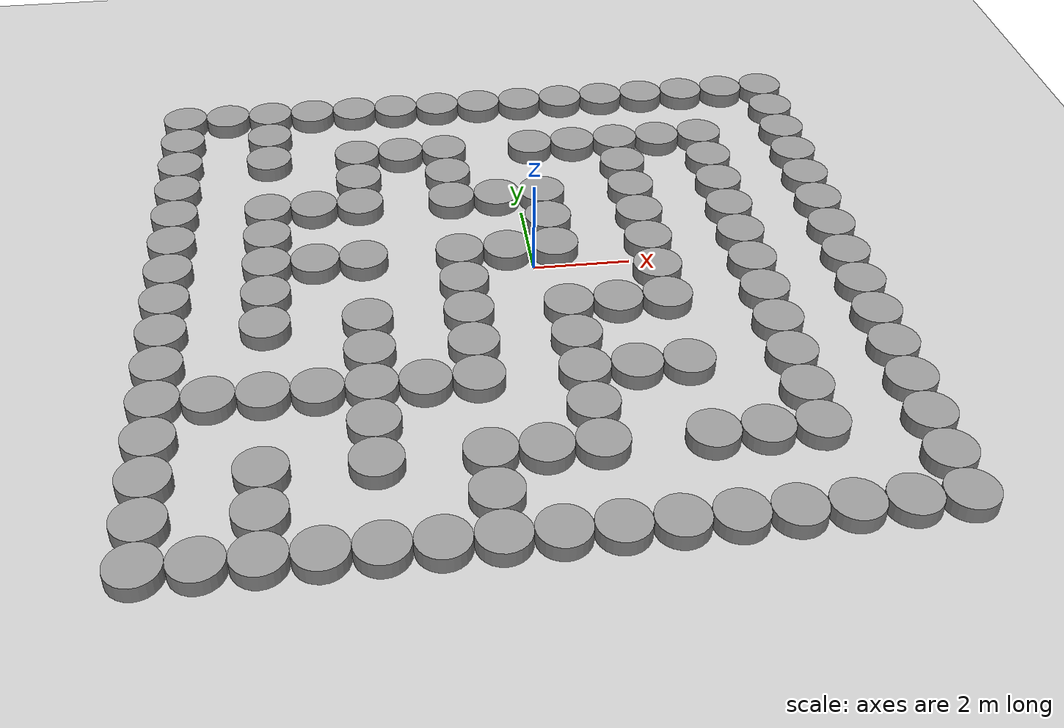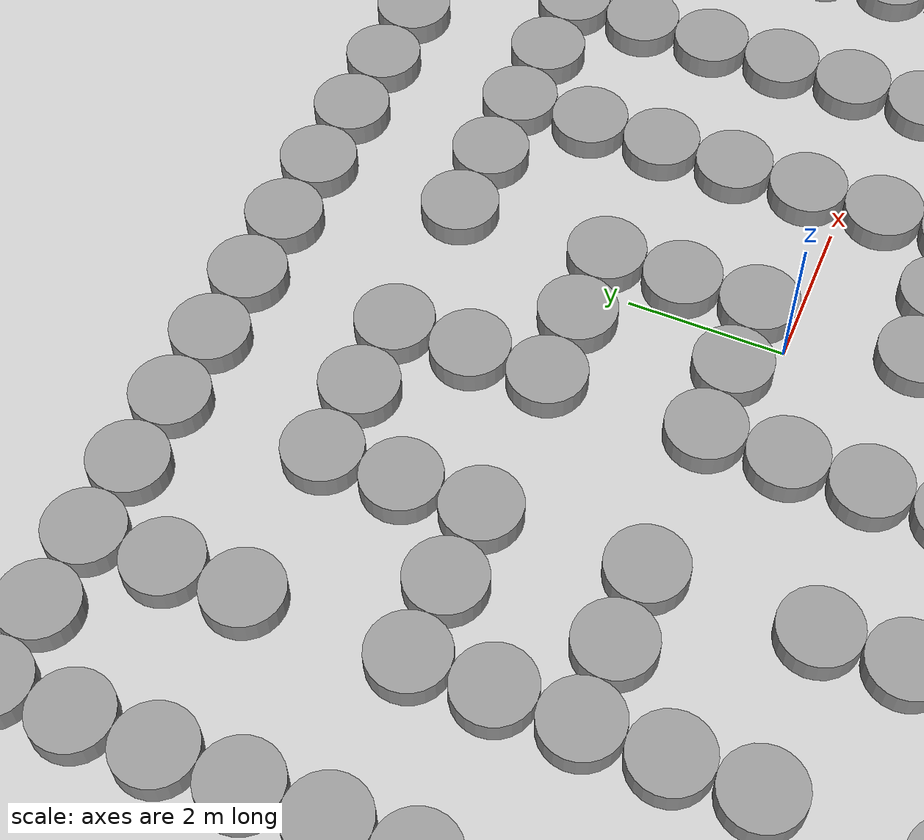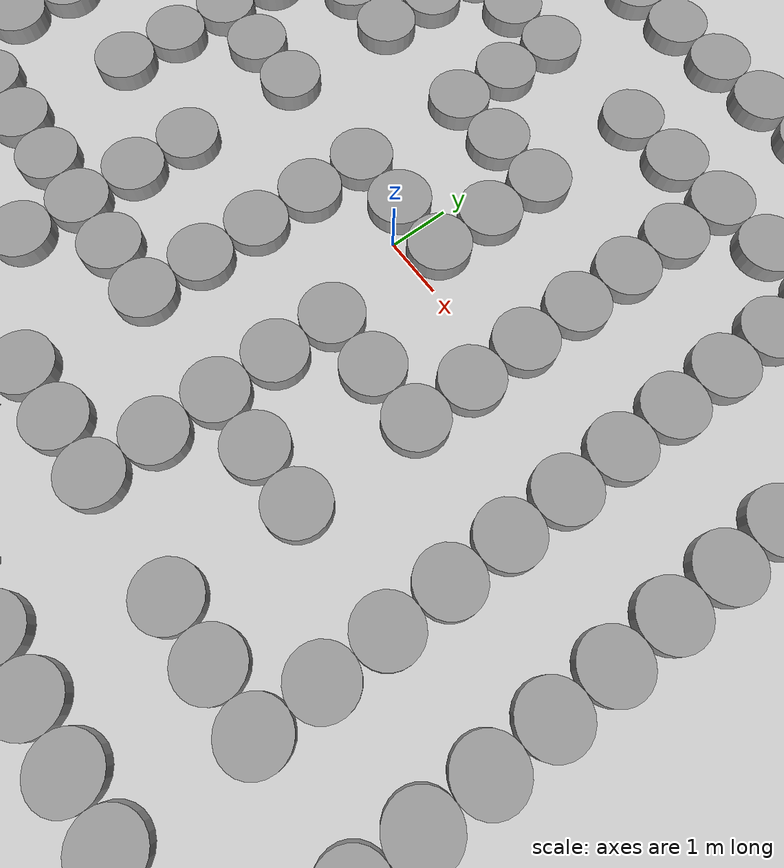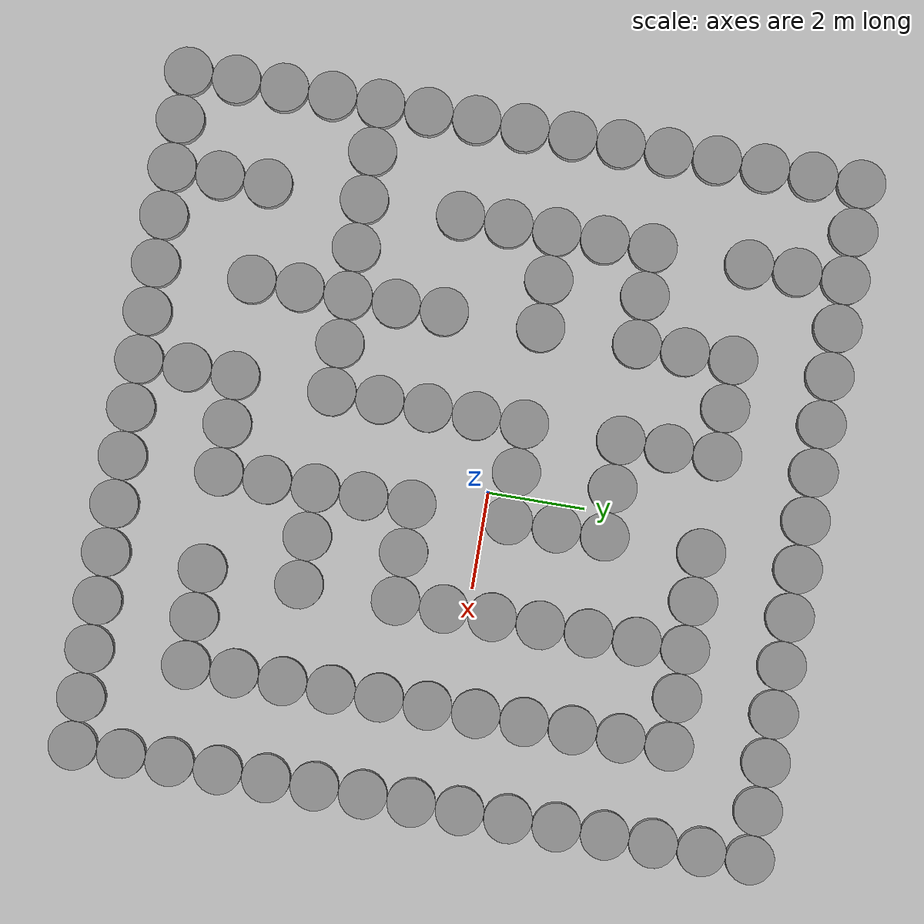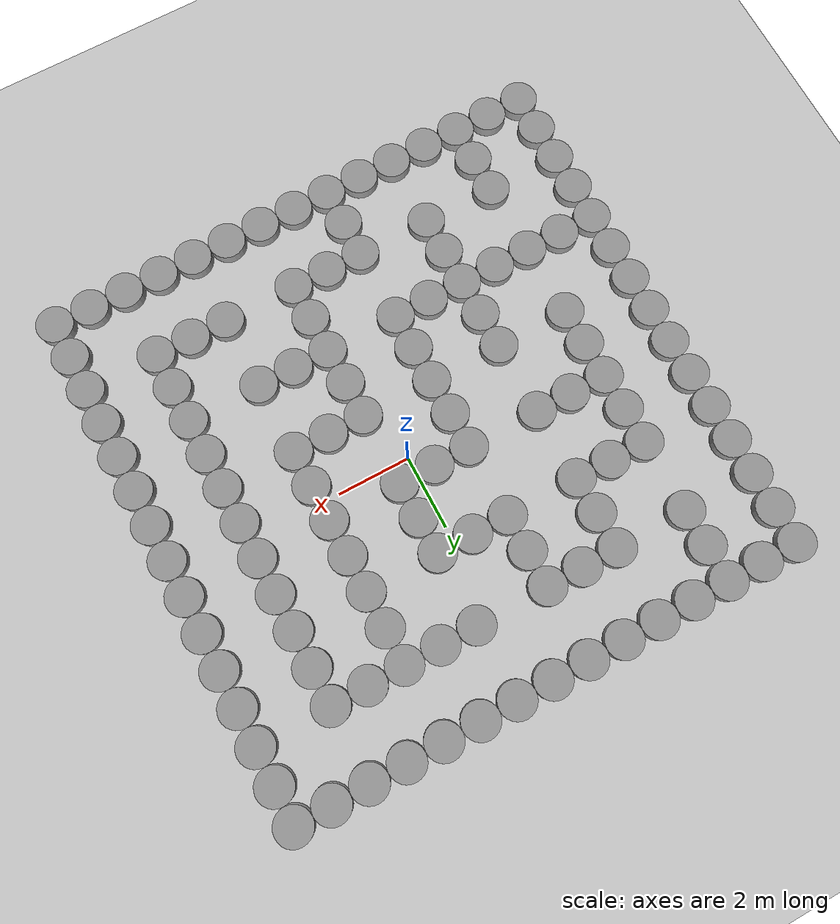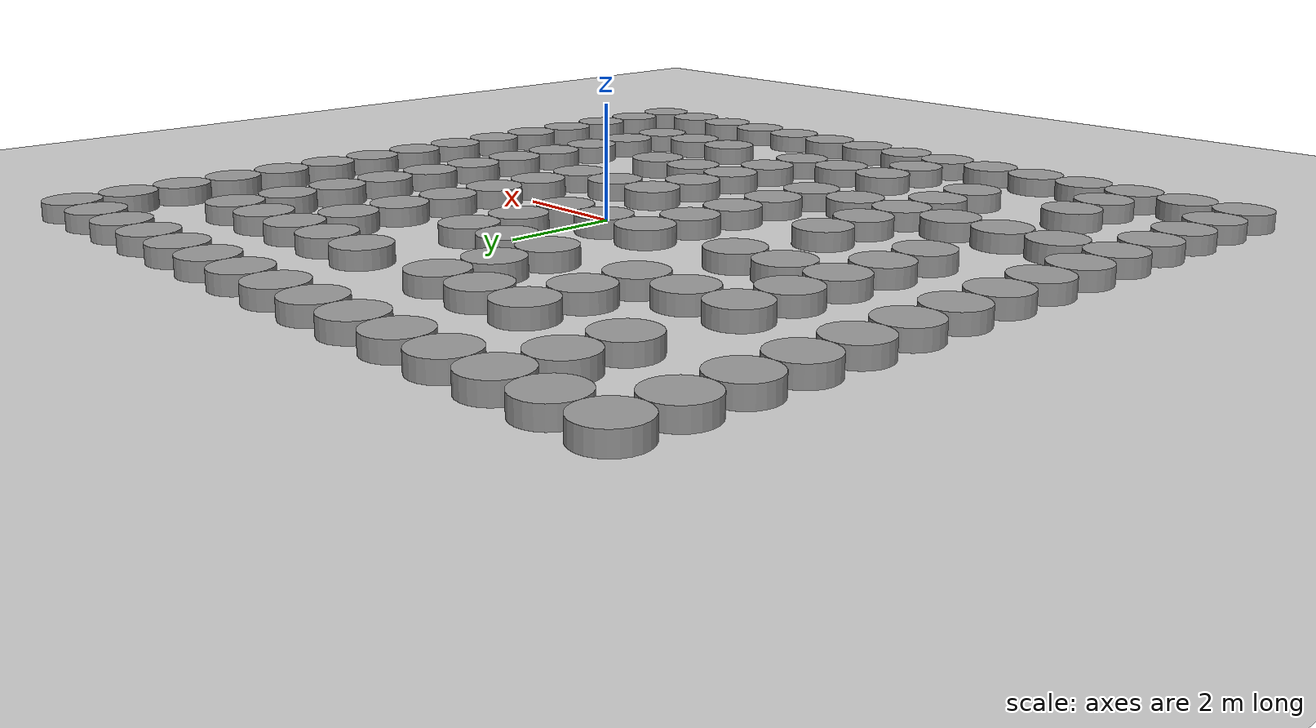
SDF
<sdf version='1.8'>
  <world name='block_maze'>
    <!-- Physics -->
    <physics name="1ms" type="ignored">
      <max_step_size>0.001</max_step_size>
      <real_time_factor>1.0</real_time_factor>
    </physics>

    <!-- Lighting -->
    <light type="directional" name="sun">
      <cast_shadows>true</cast_shadows>
      <pose>0 0 10 0 0 0</pose>
      <diffuse>0.8 0.8 0.8 1</diffuse>
      <specular>0.2 0.2 0.2 1</specular>
      <attenuation>
        <range>1000</range>
        <constant>0.9</constant>
        <linear>0.01</linear>
        <quadratic>0.001</quadratic>
      </attenuation>
      <direction>-0.5 0.1 -0.9</direction>
    </light>

    <!-- Ground plane -->
    <model name='ground_plane'>
      <static>true</static>
      <link name='link'>
        <collision name='collision'>
          <geometry>
            <plane>
              <normal>0 0 1</normal>
              <size>100 100</size>
            </plane>
          </geometry>
        </collision>
        <visual name='visual'>
          <geometry>
            <plane>
              <normal>0 0 1</normal>
              <size>100 100</size>
            </plane>
          </geometry>
          <material>
            <ambient>0.5 0.5 0.5 1</ambient>
            <diffuse>0.8 0.8 0.8 1</diffuse>
          </material>
        </visual>
      </link>
    </model>

    <model name='wall_0_0'>
      <static>true</static>
      <pose>-7.5 -7.5 0.1 0 0 0</pose>
      <link name='link'>
        <collision name='collision'>
          <geometry>
            <cylinder>
              <radius>0.5</radius>
              <length>0.4</length>
            </cylinder>
          </geometry>
        </collision>
        <visual name='visual'>
          <geometry>
            <cylinder>
              <radius>0.5</radius>
              <length>0.4</length>
            </cylinder>
          </geometry>
          <material>
            <ambient>0.6 0.6 0.6 1</ambient>
            <diffuse>0.6 0.6 0.6 1</diffuse>
          </material>
        </visual>
      </link>
    </model>

    <model name='wall_1_0'>
      <static>true</static>
      <pose>-6.5 -7.5 0.1 0 0 0</pose>
      <link name='link'>
        <collision name='collision'>
          <geometry>
            <cylinder>
              <radius>0.5</radius>
              <length>0.4</length>
            </cylinder>
          </geometry>
        </collision>
        <visual name='visual'>
          <geometry>
            <cylinder>
              <radius>0.5</radius>
              <length>0.4</length>
            </cylinder>
          </geometry>
          <material>
            <ambient>0.6 0.6 0.6 1</ambient>
            <diffuse>0.6 0.6 0.6 1</diffuse>
          </material>
        </visual>
      </link>
    </model>

    <model name='wall_2_0'>
      <static>true</static>
      <pose>-5.5 -7.5 0.1 0 0 0</pose>
      <link name='link'>
        <collision name='collision'>
          <geometry>
            <cylinder>
              <radius>0.5</radius>
              <length>0.4</length>
            </cylinder>
          </geometry>
        </collision>
        <visual name='visual'>
          <geometry>
            <cylinder>
              <radius>0.5</radius>
              <length>0.4</length>
            </cylinder>
          </geometry>
          <material>
            <ambient>0.6 0.6 0.6 1</ambient>
            <diffuse>0.6 0.6 0.6 1</diffuse>
          </material>
        </visual>
      </link>
    </model>

    <model name='wall_3_0'>
      <static>true</static>
      <pose>-4.5 -7.5 0.1 0 0 0</pose>
      <link name='link'>
        <collision name='collision'>
          <geometry>
            <cylinder>
              <radius>0.5</radius>
              <length>0.4</length>
            </cylinder>
          </geometry>
        </collision>
        <visual name='visual'>
          <geometry>
            <cylinder>
              <radius>0.5</radius>
              <length>0.4</length>
            </cylinder>
          </geometry>
          <material>
            <ambient>0.6 0.6 0.6 1</ambient>
            <diffuse>0.6 0.6 0.6 1</diffuse>
          </material>
        </visual>
      </link>
    </model>

    <model name='wall_4_0'>
      <static>true</static>
      <pose>-3.5 -7.5 0.1 0 0 0</pose>
      <link name='link'>
        <collision name='collision'>
          <geometry>
            <cylinder>
              <radius>0.5</radius>
              <length>0.4</length>
            </cylinder>
          </geometry>
        </collision>
        <visual name='visual'>
          <geometry>
            <cylinder>
              <radius>0.5</radius>
              <length>0.4</length>
            </cylinder>
          </geometry>
          <material>
            <ambient>0.6 0.6 0.6 1</ambient>
            <diffuse>0.6 0.6 0.6 1</diffuse>
          </material>
        </visual>
      </link>
    </model>

    <model name='wall_5_0'>
      <static>true</static>
      <pose>-2.5 -7.5 0.1 0 0 0</pose>
      <link name='link'>
        <collision name='collision'>
          <geometry>
            <cylinder>
              <radius>0.5</radius>
              <length>0.4</length>
            </cylinder>
          </geometry>
        </collision>
        <visual name='visual'>
          <geometry>
            <cylinder>
              <radius>0.5</radius>
              <length>0.4</length>
            </cylinder>
          </geometry>
          <material>
            <ambient>0.6 0.6 0.6 1</ambient>
            <diffuse>0.6 0.6 0.6 1</diffuse>
          </material>
        </visual>
      </link>
    </model>

    <model name='wall_6_0'>
      <static>true</static>
      <pose>-1.5 -7.5 0.1 0 0 0</pose>
      <link name='link'>
        <collision name='collision'>
          <geometry>
            <cylinder>
              <radius>0.5</radius>
              <length>0.4</length>
            </cylinder>
          </geometry>
        </collision>
        <visual name='visual'>
          <geometry>
            <cylinder>
              <radius>0.5</radius>
              <length>0.4</length>
            </cylinder>
          </geometry>
          <material>
            <ambient>0.6 0.6 0.6 1</ambient>
            <diffuse>0.6 0.6 0.6 1</diffuse>
          </material>
        </visual>
      </link>
    </model>

    <model name='wall_7_0'>
      <static>true</static>
      <pose>-0.5 -7.5 0.1 0 0 0</pose>
      <link name='link'>
        <collision name='collision'>
          <geometry>
            <cylinder>
              <radius>0.5</radius>
              <length>0.4</length>
            </cylinder>
          </geometry>
        </collision>
        <visual name='visual'>
          <geometry>
            <cylinder>
              <radius>0.5</radius>
              <length>0.4</length>
            </cylinder>
          </geometry>
          <material>
            <ambient>0.6 0.6 0.6 1</ambient>
            <diffuse>0.6 0.6 0.6 1</diffuse>
          </material>
        </visual>
      </link>
    </model>

    <model name='wall_8_0'>
      <static>true</static>
      <pose>0.5 -7.5 0.1 0 0 0</pose>
      <link name='link'>
        <collision name='collision'>
          <geometry>
            <cylinder>
              <radius>0.5</radius>
              <length>0.4</length>
            </cylinder>
          </geometry>
        </collision>
        <visual name='visual'>
          <geometry>
            <cylinder>
              <radius>0.5</radius>
              <length>0.4</length>
            </cylinder>
          </geometry>
          <material>
            <ambient>0.6 0.6 0.6 1</ambient>
            <diffuse>0.6 0.6 0.6 1</diffuse>
          </material>
        </visual>
      </link>
    </model>

    <model name='wall_9_0'>
      <static>true</static>
      <pose>1.5 -7.5 0.1 0 0 0</pose>
      <link name='link'>
        <collision name='collision'>
          <geometry>
            <cylinder>
              <radius>0.5</radius>
              <length>0.4</length>
            </cylinder>
          </geometry>
        </collision>
        <visual name='visual'>
          <geometry>
            <cylinder>
              <radius>0.5</radius>
              <length>0.4</length>
            </cylinder>
          </geometry>
          <material>
            <ambient>0.6 0.6 0.6 1</ambient>
            <diffuse>0.6 0.6 0.6 1</diffuse>
          </material>
        </visual>
      </link>
    </model>

    <model name='wall_10_0'>
      <static>true</static>
      <pose>2.5 -7.5 0.1 0 0 0</pose>
      <link name='link'>
        <collision name='collision'>
          <geometry>
            <cylinder>
              <radius>0.5</radius>
              <length>0.4</length>
            </cylinder>
          </geometry>
        </collision>
        <visual name='visual'>
          <geometry>
            <cylinder>
              <radius>0.5</radius>
              <length>0.4</length>
            </cylinder>
          </geometry>
          <material>
            <ambient>0.6 0.6 0.6 1</ambient>
            <diffuse>0.6 0.6 0.6 1</diffuse>
          </material>
        </visual>
      </link>
    </model>

    <model name='wall_11_0'>
      <static>true</static>
      <pose>3.5 -7.5 0.1 0 0 0</pose>
      <link name='link'>
        <collision name='collision'>
          <geometry>
            <cylinder>
              <radius>0.5</radius>
              <length>0.4</length>
            </cylinder>
          </geometry>
        </collision>
        <visual name='visual'>
          <geometry>
            <cylinder>
              <radius>0.5</radius>
              <length>0.4</length>
            </cylinder>
          </geometry>
          <material>
            <ambient>0.6 0.6 0.6 1</ambient>
            <diffuse>0.6 0.6 0.6 1</diffuse>
          </material>
        </visual>
      </link>
    </model>

    <model name='wall_12_0'>
      <static>true</static>
      <pose>4.5 -7.5 0.1 0 0 0</pose>
      <link name='link'>
        <collision name='collision'>
          <geometry>
            <cylinder>
              <radius>0.5</radius>
              <length>0.4</length>
            </cylinder>
          </geometry>
        </collision>
        <visual name='visual'>
          <geometry>
            <cylinder>
              <radius>0.5</radius>
              <length>0.4</length>
            </cylinder>
          </geometry>
          <material>
            <ambient>0.6 0.6 0.6 1</ambient>
            <diffuse>0.6 0.6 0.6 1</diffuse>
          </material>
        </visual>
      </link>
    </model>

    <model name='wall_13_0'>
      <static>true</static>
      <pose>5.5 -7.5 0.1 0 0 0</pose>
      <link name='link'>
        <collision name='collision'>
          <geometry>
            <cylinder>
              <radius>0.5</radius>
              <length>0.4</length>
            </cylinder>
          </geometry>
        </collision>
        <visual name='visual'>
          <geometry>
            <cylinder>
              <radius>0.5</radius>
              <length>0.4</length>
            </cylinder>
          </geometry>
          <material>
            <ambient>0.6 0.6 0.6 1</ambient>
            <diffuse>0.6 0.6 0.6 1</diffuse>
          </material>
        </visual>
      </link>
    </model>

    <model name='wall_14_0'>
      <static>true</static>
      <pose>6.5 -7.5 0.1 0 0 0</pose>
      <link name='link'>
        <collision name='collision'>
          <geometry>
            <cylinder>
              <radius>0.5</radius>
              <length>0.4</length>
            </cylinder>
          </geometry>
        </collision>
        <visual name='visual'>
          <geometry>
            <cylinder>
              <radius>0.5</radius>
              <length>0.4</length>
            </cylinder>
          </geometry>
          <material>
            <ambient>0.6 0.6 0.6 1</ambient>
            <diffuse>0.6 0.6 0.6 1</diffuse>
          </material>
        </visual>
      </link>
    </model>

    <model name='wall_0_1'>
      <static>true</static>
      <pose>-7.5 -6.5 0.1 0 0 0</pose>
      <link name='link'>
        <collision name='collision'>
          <geometry>
            <cylinder>
              <radius>0.5</radius>
              <length>0.4</length>
            </cylinder>
          </geometry>
        </collision>
        <visual name='visual'>
          <geometry>
            <cylinder>
              <radius>0.5</radius>
              <length>0.4</length>
            </cylinder>
          </geometry>
          <material>
            <ambient>0.6 0.6 0.6 1</ambient>
            <diffuse>0.6 0.6 0.6 1</diffuse>
          </material>
        </visual>
      </link>
    </model>

    <model name='wall_2_1'>
      <static>true</static>
      <pose>-5.5 -6.5 0.1 0 0 0</pose>
      <link name='link'>
        <collision name='collision'>
          <geometry>
            <cylinder>
              <radius>0.5</radius>
              <length>0.4</length>
            </cylinder>
          </geometry>
        </collision>
        <visual name='visual'>
          <geometry>
            <cylinder>
              <radius>0.5</radius>
              <length>0.4</length>
            </cylinder>
          </geometry>
          <material>
            <ambient>0.6 0.6 0.6 1</ambient>
            <diffuse>0.6 0.6 0.6 1</diffuse>
          </material>
        </visual>
      </link>
    </model>

    <model name='wall_6_1'>
      <static>true</static>
      <pose>-1.5 -6.5 0.1 0 0 0</pose>
      <link name='link'>
        <collision name='collision'>
          <geometry>
            <cylinder>
              <radius>0.5</radius>
              <length>0.4</length>
            </cylinder>
          </geometry>
        </collision>
        <visual name='visual'>
          <geometry>
            <cylinder>
              <radius>0.5</radius>
              <length>0.4</length>
            </cylinder>
          </geometry>
          <material>
            <ambient>0.6 0.6 0.6 1</ambient>
            <diffuse>0.6 0.6 0.6 1</diffuse>
          </material>
        </visual>
      </link>
    </model>

    <model name='wall_14_1'>
      <static>true</static>
      <pose>6.5 -6.5 0.1 0 0 0</pose>
      <link name='link'>
        <collision name='collision'>
          <geometry>
            <cylinder>
              <radius>0.5</radius>
              <length>0.4</length>
            </cylinder>
          </geometry>
        </collision>
        <visual name='visual'>
          <geometry>
            <cylinder>
              <radius>0.5</radius>
              <length>0.4</length>
            </cylinder>
          </geometry>
          <material>
            <ambient>0.6 0.6 0.6 1</ambient>
            <diffuse>0.6 0.6 0.6 1</diffuse>
          </material>
        </visual>
      </link>
    </model>

    <model name='wall_0_2'>
      <static>true</static>
      <pose>-7.5 -5.5 0.1 0 0 0</pose>
      <link name='link'>
        <collision name='collision'>
          <geometry>
            <cylinder>
              <radius>0.5</radius>
              <length>0.4</length>
            </cylinder>
          </geometry>
        </collision>
        <visual name='visual'>
          <geometry>
            <cylinder>
              <radius>0.5</radius>
              <length>0.4</length>
            </cylinder>
          </geometry>
          <material>
            <ambient>0.6 0.6 0.6 1</ambient>
            <diffuse>0.6 0.6 0.6 1</diffuse>
          </material>
        </visual>
      </link>
    </model>

    <model name='wall_2_2'>
      <static>true</static>
      <pose>-5.5 -5.5 0.1 0 0 0</pose>
      <link name='link'>
        <collision name='collision'>
          <geometry>
            <cylinder>
              <radius>0.5</radius>
              <length>0.4</length>
            </cylinder>
          </geometry>
        </collision>
        <visual name='visual'>
          <geometry>
            <cylinder>
              <radius>0.5</radius>
              <length>0.4</length>
            </cylinder>
          </geometry>
          <material>
            <ambient>0.6 0.6 0.6 1</ambient>
            <diffuse>0.6 0.6 0.6 1</diffuse>
          </material>
        </visual>
      </link>
    </model>

    <model name='wall_4_2'>
      <static>true</static>
      <pose>-3.5 -5.5 0.1 0 0 0</pose>
      <link name='link'>
        <collision name='collision'>
          <geometry>
            <cylinder>
              <radius>0.5</radius>
              <length>0.4</length>
            </cylinder>
          </geometry>
        </collision>
        <visual name='visual'>
          <geometry>
            <cylinder>
              <radius>0.5</radius>
              <length>0.4</length>
            </cylinder>
          </geometry>
          <material>
            <ambient>0.6 0.6 0.6 1</ambient>
            <diffuse>0.6 0.6 0.6 1</diffuse>
          </material>
        </visual>
      </link>
    </model>

    <model name='wall_6_2'>
      <static>true</static>
      <pose>-1.5 -5.5 0.1 0 0 0</pose>
      <link name='link'>
        <collision name='collision'>
          <geometry>
            <cylinder>
              <radius>0.5</radius>
              <length>0.4</length>
            </cylinder>
          </geometry>
        </collision>
        <visual name='visual'>
          <geometry>
            <cylinder>
              <radius>0.5</radius>
              <length>0.4</length>
            </cylinder>
          </geometry>
          <material>
            <ambient>0.6 0.6 0.6 1</ambient>
            <diffuse>0.6 0.6 0.6 1</diffuse>
          </material>
        </visual>
      </link>
    </model>

    <model name='wall_7_2'>
      <static>true</static>
      <pose>-0.5 -5.5 0.1 0 0 0</pose>
      <link name='link'>
        <collision name='collision'>
          <geometry>
            <cylinder>
              <radius>0.5</radius>
              <length>0.4</length>
            </cylinder>
          </geometry>
        </collision>
        <visual name='visual'>
          <geometry>
            <cylinder>
              <radius>0.5</radius>
              <length>0.4</length>
            </cylinder>
          </geometry>
          <material>
            <ambient>0.6 0.6 0.6 1</ambient>
            <diffuse>0.6 0.6 0.6 1</diffuse>
          </material>
        </visual>
      </link>
    </model>

    <model name='wall_8_2'>
      <static>true</static>
      <pose>0.5 -5.5 0.1 0 0 0</pose>
      <link name='link'>
        <collision name='collision'>
          <geometry>
            <cylinder>
              <radius>0.5</radius>
              <length>0.4</length>
            </cylinder>
          </geometry>
        </collision>
        <visual name='visual'>
          <geometry>
            <cylinder>
              <radius>0.5</radius>
              <length>0.4</length>
            </cylinder>
          </geometry>
          <material>
            <ambient>0.6 0.6 0.6 1</ambient>
            <diffuse>0.6 0.6 0.6 1</diffuse>
          </material>
        </visual>
      </link>
    </model>

    <model name='wall_10_2'>
      <static>true</static>
      <pose>2.5 -5.5 0.1 0 0 0</pose>
      <link name='link'>
        <collision name='collision'>
          <geometry>
            <cylinder>
              <radius>0.5</radius>
              <length>0.4</length>
            </cylinder>
          </geometry>
        </collision>
        <visual name='visual'>
          <geometry>
            <cylinder>
              <radius>0.5</radius>
              <length>0.4</length>
            </cylinder>
          </geometry>
          <material>
            <ambient>0.6 0.6 0.6 1</ambient>
            <diffuse>0.6 0.6 0.6 1</diffuse>
          </material>
        </visual>
      </link>
    </model>

    <model name='wall_11_2'>
      <static>true</static>
      <pose>3.5 -5.5 0.1 0 0 0</pose>
      <link name='link'>
        <collision name='collision'>
          <geometry>
            <cylinder>
              <radius>0.5</radius>
              <length>0.4</length>
            </cylinder>
          </geometry>
        </collision>
        <visual name='visual'>
          <geometry>
            <cylinder>
              <radius>0.5</radius>
              <length>0.4</length>
            </cylinder>
          </geometry>
          <material>
            <ambient>0.6 0.6 0.6 1</ambient>
            <diffuse>0.6 0.6 0.6 1</diffuse>
          </material>
        </visual>
      </link>
    </model>

    <model name='wall_12_2'>
      <static>true</static>
      <pose>4.5 -5.5 0.1 0 0 0</pose>
      <link name='link'>
        <collision name='collision'>
          <geometry>
            <cylinder>
              <radius>0.5</radius>
              <length>0.4</length>
            </cylinder>
          </geometry>
        </collision>
        <visual name='visual'>
          <geometry>
            <cylinder>
              <radius>0.5</radius>
              <length>0.4</length>
            </cylinder>
          </geometry>
          <material>
            <ambient>0.6 0.6 0.6 1</ambient>
            <diffuse>0.6 0.6 0.6 1</diffuse>
          </material>
        </visual>
      </link>
    </model>

    <model name='wall_14_2'>
      <static>true</static>
      <pose>6.5 -5.5 0.1 0 0 0</pose>
      <link name='link'>
        <collision name='collision'>
          <geometry>
            <cylinder>
              <radius>0.5</radius>
              <length>0.4</length>
            </cylinder>
          </geometry>
        </collision>
        <visual name='visual'>
          <geometry>
            <cylinder>
              <radius>0.5</radius>
              <length>0.4</length>
            </cylinder>
          </geometry>
          <material>
            <ambient>0.6 0.6 0.6 1</ambient>
            <diffuse>0.6 0.6 0.6 1</diffuse>
          </material>
        </visual>
      </link>
    </model>

    <model name='wall_0_3'>
      <static>true</static>
      <pose>-7.5 -4.5 0.1 0 0 0</pose>
      <link name='link'>
        <collision name='collision'>
          <geometry>
            <cylinder>
              <radius>0.5</radius>
              <length>0.4</length>
            </cylinder>
          </geometry>
        </collision>
        <visual name='visual'>
          <geometry>
            <cylinder>
              <radius>0.5</radius>
              <length>0.4</length>
            </cylinder>
          </geometry>
          <material>
            <ambient>0.6 0.6 0.6 1</ambient>
            <diffuse>0.6 0.6 0.6 1</diffuse>
          </material>
        </visual>
      </link>
    </model>

    <model name='wall_4_3'>
      <static>true</static>
      <pose>-3.5 -4.5 0.1 0 0 0</pose>
      <link name='link'>
        <collision name='collision'>
          <geometry>
            <cylinder>
              <radius>0.5</radius>
              <length>0.4</length>
            </cylinder>
          </geometry>
        </collision>
        <visual name='visual'>
          <geometry>
            <cylinder>
              <radius>0.5</radius>
              <length>0.4</length>
            </cylinder>
          </geometry>
          <material>
            <ambient>0.6 0.6 0.6 1</ambient>
            <diffuse>0.6 0.6 0.6 1</diffuse>
          </material>
        </visual>
      </link>
    </model>

    <model name='wall_8_3'>
      <static>true</static>
      <pose>0.5 -4.5 0.1 0 0 0</pose>
      <link name='link'>
        <collision name='collision'>
          <geometry>
            <cylinder>
              <radius>0.5</radius>
              <length>0.4</length>
            </cylinder>
          </geometry>
        </collision>
        <visual name='visual'>
          <geometry>
            <cylinder>
              <radius>0.5</radius>
              <length>0.4</length>
            </cylinder>
          </geometry>
          <material>
            <ambient>0.6 0.6 0.6 1</ambient>
            <diffuse>0.6 0.6 0.6 1</diffuse>
          </material>
        </visual>
      </link>
    </model>

    <model name='wall_12_3'>
      <static>true</static>
      <pose>4.5 -4.5 0.1 0 0 0</pose>
      <link name='link'>
        <collision name='collision'>
          <geometry>
            <cylinder>
              <radius>0.5</radius>
              <length>0.4</length>
            </cylinder>
          </geometry>
        </collision>
        <visual name='visual'>
          <geometry>
            <cylinder>
              <radius>0.5</radius>
              <length>0.4</length>
            </cylinder>
          </geometry>
          <material>
            <ambient>0.6 0.6 0.6 1</ambient>
            <diffuse>0.6 0.6 0.6 1</diffuse>
          </material>
        </visual>
      </link>
    </model>

    <model name='wall_14_3'>
      <static>true</static>
      <pose>6.5 -4.5 0.1 0 0 0</pose>
      <link name='link'>
        <collision name='collision'>
          <geometry>
            <cylinder>
              <radius>0.5</radius>
              <length>0.4</length>
            </cylinder>
          </geometry>
        </collision>
        <visual name='visual'>
          <geometry>
            <cylinder>
              <radius>0.5</radius>
              <length>0.4</length>
            </cylinder>
          </geometry>
          <material>
            <ambient>0.6 0.6 0.6 1</ambient>
            <diffuse>0.6 0.6 0.6 1</diffuse>
          </material>
        </visual>
      </link>
    </model>

    <model name='wall_0_4'>
      <static>true</static>
      <pose>-7.5 -3.5 0.1 0 0 0</pose>
      <link name='link'>
        <collision name='collision'>
          <geometry>
            <cylinder>
              <radius>0.5</radius>
              <length>0.4</length>
            </cylinder>
          </geometry>
        </collision>
        <visual name='visual'>
          <geometry>
            <cylinder>
              <radius>0.5</radius>
              <length>0.4</length>
            </cylinder>
          </geometry>
          <material>
            <ambient>0.6 0.6 0.6 1</ambient>
            <diffuse>0.6 0.6 0.6 1</diffuse>
          </material>
        </visual>
      </link>
    </model>

    <model name='wall_1_4'>
      <static>true</static>
      <pose>-6.5 -3.5 0.1 0 0 0</pose>
      <link name='link'>
        <collision name='collision'>
          <geometry>
            <cylinder>
              <radius>0.5</radius>
              <length>0.4</length>
            </cylinder>
          </geometry>
        </collision>
        <visual name='visual'>
          <geometry>
            <cylinder>
              <radius>0.5</radius>
              <length>0.4</length>
            </cylinder>
          </geometry>
          <material>
            <ambient>0.6 0.6 0.6 1</ambient>
            <diffuse>0.6 0.6 0.6 1</diffuse>
          </material>
        </visual>
      </link>
    </model>

    <model name='wall_2_4'>
      <static>true</static>
      <pose>-5.5 -3.5 0.1 0 0 0</pose>
      <link name='link'>
        <collision name='collision'>
          <geometry>
            <cylinder>
              <radius>0.5</radius>
              <length>0.4</length>
            </cylinder>
          </geometry>
        </collision>
        <visual name='visual'>
          <geometry>
            <cylinder>
              <radius>0.5</radius>
              <length>0.4</length>
            </cylinder>
          </geometry>
          <material>
            <ambient>0.6 0.6 0.6 1</ambient>
            <diffuse>0.6 0.6 0.6 1</diffuse>
          </material>
        </visual>
      </link>
    </model>

    <model name='wall_3_4'>
      <static>true</static>
      <pose>-4.5 -3.5 0.1 0 0 0</pose>
      <link name='link'>
        <collision name='collision'>
          <geometry>
            <cylinder>
              <radius>0.5</radius>
              <length>0.4</length>
            </cylinder>
          </geometry>
        </collision>
        <visual name='visual'>
          <geometry>
            <cylinder>
              <radius>0.5</radius>
              <length>0.4</length>
            </cylinder>
          </geometry>
          <material>
            <ambient>0.6 0.6 0.6 1</ambient>
            <diffuse>0.6 0.6 0.6 1</diffuse>
          </material>
        </visual>
      </link>
    </model>

    <model name='wall_4_4'>
      <static>true</static>
      <pose>-3.5 -3.5 0.1 0 0 0</pose>
      <link name='link'>
        <collision name='collision'>
          <geometry>
            <cylinder>
              <radius>0.5</radius>
              <length>0.4</length>
            </cylinder>
          </geometry>
        </collision>
        <visual name='visual'>
          <geometry>
            <cylinder>
              <radius>0.5</radius>
              <length>0.4</length>
            </cylinder>
          </geometry>
          <material>
            <ambient>0.6 0.6 0.6 1</ambient>
            <diffuse>0.6 0.6 0.6 1</diffuse>
          </material>
        </visual>
      </link>
    </model>

    <model name='wall_5_4'>
      <static>true</static>
      <pose>-2.5 -3.5 0.1 0 0 0</pose>
      <link name='link'>
        <collision name='collision'>
          <geometry>
            <cylinder>
              <radius>0.5</radius>
              <length>0.4</length>
            </cylinder>
          </geometry>
        </collision>
        <visual name='visual'>
          <geometry>
            <cylinder>
              <radius>0.5</radius>
              <length>0.4</length>
            </cylinder>
          </geometry>
          <material>
            <ambient>0.6 0.6 0.6 1</ambient>
            <diffuse>0.6 0.6 0.6 1</diffuse>
          </material>
        </visual>
      </link>
    </model>

    <model name='wall_6_4'>
      <static>true</static>
      <pose>-1.5 -3.5 0.1 0 0 0</pose>
      <link name='link'>
        <collision name='collision'>
          <geometry>
            <cylinder>
              <radius>0.5</radius>
              <length>0.4</length>
            </cylinder>
          </geometry>
        </collision>
        <visual name='visual'>
          <geometry>
            <cylinder>
              <radius>0.5</radius>
              <length>0.4</length>
            </cylinder>
          </geometry>
          <material>
            <ambient>0.6 0.6 0.6 1</ambient>
            <diffuse>0.6 0.6 0.6 1</diffuse>
          </material>
        </visual>
      </link>
    </model>

    <model name='wall_8_4'>
      <static>true</static>
      <pose>0.5 -3.5 0.1 0 0 0</pose>
      <link name='link'>
        <collision name='collision'>
          <geometry>
            <cylinder>
              <radius>0.5</radius>
              <length>0.4</length>
            </cylinder>
          </geometry>
        </collision>
        <visual name='visual'>
          <geometry>
            <cylinder>
              <radius>0.5</radius>
              <length>0.4</length>
            </cylinder>
          </geometry>
          <material>
            <ambient>0.6 0.6 0.6 1</ambient>
            <diffuse>0.6 0.6 0.6 1</diffuse>
          </material>
        </visual>
      </link>
    </model>

    <model name='wall_9_4'>
      <static>true</static>
      <pose>1.5 -3.5 0.1 0 0 0</pose>
      <link name='link'>
        <collision name='collision'>
          <geometry>
            <cylinder>
              <radius>0.5</radius>
              <length>0.4</length>
            </cylinder>
          </geometry>
        </collision>
        <visual name='visual'>
          <geometry>
            <cylinder>
              <radius>0.5</radius>
              <length>0.4</length>
            </cylinder>
          </geometry>
          <material>
            <ambient>0.6 0.6 0.6 1</ambient>
            <diffuse>0.6 0.6 0.6 1</diffuse>
          </material>
        </visual>
      </link>
    </model>

    <model name='wall_10_4'>
      <static>true</static>
      <pose>2.5 -3.5 0.1 0 0 0</pose>
      <link name='link'>
        <collision name='collision'>
          <geometry>
            <cylinder>
              <radius>0.5</radius>
              <length>0.4</length>
            </cylinder>
          </geometry>
        </collision>
        <visual name='visual'>
          <geometry>
            <cylinder>
              <radius>0.5</radius>
              <length>0.4</length>
            </cylinder>
          </geometry>
          <material>
            <ambient>0.6 0.6 0.6 1</ambient>
            <diffuse>0.6 0.6 0.6 1</diffuse>
          </material>
        </visual>
      </link>
    </model>

    <model name='wall_12_4'>
      <static>true</static>
      <pose>4.5 -3.5 0.1 0 0 0</pose>
      <link name='link'>
        <collision name='collision'>
          <geometry>
            <cylinder>
              <radius>0.5</radius>
              <length>0.4</length>
            </cylinder>
          </geometry>
        </collision>
        <visual name='visual'>
          <geometry>
            <cylinder>
              <radius>0.5</radius>
              <length>0.4</length>
            </cylinder>
          </geometry>
          <material>
            <ambient>0.6 0.6 0.6 1</ambient>
            <diffuse>0.6 0.6 0.6 1</diffuse>
          </material>
        </visual>
      </link>
    </model>

    <model name='wall_14_4'>
      <static>true</static>
      <pose>6.5 -3.5 0.1 0 0 0</pose>
      <link name='link'>
        <collision name='collision'>
          <geometry>
            <cylinder>
              <radius>0.5</radius>
              <length>0.4</length>
            </cylinder>
          </geometry>
        </collision>
        <visual name='visual'>
          <geometry>
            <cylinder>
              <radius>0.5</radius>
              <length>0.4</length>
            </cylinder>
          </geometry>
          <material>
            <ambient>0.6 0.6 0.6 1</ambient>
            <diffuse>0.6 0.6 0.6 1</diffuse>
          </material>
        </visual>
      </link>
    </model>

    <model name='wall_0_5'>
      <static>true</static>
      <pose>-7.5 -2.5 0.1 0 0 0</pose>
      <link name='link'>
        <collision name='collision'>
          <geometry>
            <cylinder>
              <radius>0.5</radius>
              <length>0.4</length>
            </cylinder>
          </geometry>
        </collision>
        <visual name='visual'>
          <geometry>
            <cylinder>
              <radius>0.5</radius>
              <length>0.4</length>
            </cylinder>
          </geometry>
          <material>
            <ambient>0.6 0.6 0.6 1</ambient>
            <diffuse>0.6 0.6 0.6 1</diffuse>
          </material>
        </visual>
      </link>
    </model>

    <model name='wall_4_5'>
      <static>true</static>
      <pose>-3.5 -2.5 0.1 0 0 0</pose>
      <link name='link'>
        <collision name='collision'>
          <geometry>
            <cylinder>
              <radius>0.5</radius>
              <length>0.4</length>
            </cylinder>
          </geometry>
        </collision>
        <visual name='visual'>
          <geometry>
            <cylinder>
              <radius>0.5</radius>
              <length>0.4</length>
            </cylinder>
          </geometry>
          <material>
            <ambient>0.6 0.6 0.6 1</ambient>
            <diffuse>0.6 0.6 0.6 1</diffuse>
          </material>
        </visual>
      </link>
    </model>

    <model name='wall_6_5'>
      <static>true</static>
      <pose>-1.5 -2.5 0.1 0 0 0</pose>
      <link name='link'>
        <collision name='collision'>
          <geometry>
            <cylinder>
              <radius>0.5</radius>
              <length>0.4</length>
            </cylinder>
          </geometry>
        </collision>
        <visual name='visual'>
          <geometry>
            <cylinder>
              <radius>0.5</radius>
              <length>0.4</length>
            </cylinder>
          </geometry>
          <material>
            <ambient>0.6 0.6 0.6 1</ambient>
            <diffuse>0.6 0.6 0.6 1</diffuse>
          </material>
        </visual>
      </link>
    </model>

    <model name='wall_8_5'>
      <static>true</static>
      <pose>0.5 -2.5 0.1 0 0 0</pose>
      <link name='link'>
        <collision name='collision'>
          <geometry>
            <cylinder>
              <radius>0.5</radius>
              <length>0.4</length>
            </cylinder>
          </geometry>
        </collision>
        <visual name='visual'>
          <geometry>
            <cylinder>
              <radius>0.5</radius>
              <length>0.4</length>
            </cylinder>
          </geometry>
          <material>
            <ambient>0.6 0.6 0.6 1</ambient>
            <diffuse>0.6 0.6 0.6 1</diffuse>
          </material>
        </visual>
      </link>
    </model>

    <model name='wall_12_5'>
      <static>true</static>
      <pose>4.5 -2.5 0.1 0 0 0</pose>
      <link name='link'>
        <collision name='collision'>
          <geometry>
            <cylinder>
              <radius>0.5</radius>
              <length>0.4</length>
            </cylinder>
          </geometry>
        </collision>
        <visual name='visual'>
          <geometry>
            <cylinder>
              <radius>0.5</radius>
              <length>0.4</length>
            </cylinder>
          </geometry>
          <material>
            <ambient>0.6 0.6 0.6 1</ambient>
            <diffuse>0.6 0.6 0.6 1</diffuse>
          </material>
        </visual>
      </link>
    </model>

    <model name='wall_14_5'>
      <static>true</static>
      <pose>6.5 -2.5 0.1 0 0 0</pose>
      <link name='link'>
        <collision name='collision'>
          <geometry>
            <cylinder>
              <radius>0.5</radius>
              <length>0.4</length>
            </cylinder>
          </geometry>
        </collision>
        <visual name='visual'>
          <geometry>
            <cylinder>
              <radius>0.5</radius>
              <length>0.4</length>
            </cylinder>
          </geometry>
          <material>
            <ambient>0.6 0.6 0.6 1</ambient>
            <diffuse>0.6 0.6 0.6 1</diffuse>
          </material>
        </visual>
      </link>
    </model>

    <model name='wall_0_6'>
      <static>true</static>
      <pose>-7.5 -1.5 0.1 0 0 0</pose>
      <link name='link'>
        <collision name='collision'>
          <geometry>
            <cylinder>
              <radius>0.5</radius>
              <length>0.4</length>
            </cylinder>
          </geometry>
        </collision>
        <visual name='visual'>
          <geometry>
            <cylinder>
              <radius>0.5</radius>
              <length>0.4</length>
            </cylinder>
          </geometry>
          <material>
            <ambient>0.6 0.6 0.6 1</ambient>
            <diffuse>0.6 0.6 0.6 1</diffuse>
          </material>
        </visual>
      </link>
    </model>

    <model name='wall_2_6'>
      <static>true</static>
      <pose>-5.5 -1.5 0.1 0 0 0</pose>
      <link name='link'>
        <collision name='collision'>
          <geometry>
            <cylinder>
              <radius>0.5</radius>
              <length>0.4</length>
            </cylinder>
          </geometry>
        </collision>
        <visual name='visual'>
          <geometry>
            <cylinder>
              <radius>0.5</radius>
              <length>0.4</length>
            </cylinder>
          </geometry>
          <material>
            <ambient>0.6 0.6 0.6 1</ambient>
            <diffuse>0.6 0.6 0.6 1</diffuse>
          </material>
        </visual>
      </link>
    </model>

    <model name='wall_4_6'>
      <static>true</static>
      <pose>-3.5 -1.5 0.1 0 0 0</pose>
      <link name='link'>
        <collision name='collision'>
          <geometry>
            <cylinder>
              <radius>0.5</radius>
              <length>0.4</length>
            </cylinder>
          </geometry>
        </collision>
        <visual name='visual'>
          <geometry>
            <cylinder>
              <radius>0.5</radius>
              <length>0.4</length>
            </cylinder>
          </geometry>
          <material>
            <ambient>0.6 0.6 0.6 1</ambient>
            <diffuse>0.6 0.6 0.6 1</diffuse>
          </material>
        </visual>
      </link>
    </model>

    <model name='wall_6_6'>
      <static>true</static>
      <pose>-1.5 -1.5 0.1 0 0 0</pose>
      <link name='link'>
        <collision name='collision'>
          <geometry>
            <cylinder>
              <radius>0.5</radius>
              <length>0.4</length>
            </cylinder>
          </geometry>
        </collision>
        <visual name='visual'>
          <geometry>
            <cylinder>
              <radius>0.5</radius>
              <length>0.4</length>
            </cylinder>
          </geometry>
          <material>
            <ambient>0.6 0.6 0.6 1</ambient>
            <diffuse>0.6 0.6 0.6 1</diffuse>
          </material>
        </visual>
      </link>
    </model>

    <model name='wall_8_6'>
      <static>true</static>
      <pose>0.5 -1.5 0.1 0 0 0</pose>
      <link name='link'>
        <collision name='collision'>
          <geometry>
            <cylinder>
              <radius>0.5</radius>
              <length>0.4</length>
            </cylinder>
          </geometry>
        </collision>
        <visual name='visual'>
          <geometry>
            <cylinder>
              <radius>0.5</radius>
              <length>0.4</length>
            </cylinder>
          </geometry>
          <material>
            <ambient>0.6 0.6 0.6 1</ambient>
            <diffuse>0.6 0.6 0.6 1</diffuse>
          </material>
        </visual>
      </link>
    </model>

    <model name='wall_9_6'>
      <static>true</static>
      <pose>1.5 -1.5 0.1 0 0 0</pose>
      <link name='link'>
        <collision name='collision'>
          <geometry>
            <cylinder>
              <radius>0.5</radius>
              <length>0.4</length>
            </cylinder>
          </geometry>
        </collision>
        <visual name='visual'>
          <geometry>
            <cylinder>
              <radius>0.5</radius>
              <length>0.4</length>
            </cylinder>
          </geometry>
          <material>
            <ambient>0.6 0.6 0.6 1</ambient>
            <diffuse>0.6 0.6 0.6 1</diffuse>
          </material>
        </visual>
      </link>
    </model>

    <model name='wall_10_6'>
      <static>true</static>
      <pose>2.5 -1.5 0.1 0 0 0</pose>
      <link name='link'>
        <collision name='collision'>
          <geometry>
            <cylinder>
              <radius>0.5</radius>
              <length>0.4</length>
            </cylinder>
          </geometry>
        </collision>
        <visual name='visual'>
          <geometry>
            <cylinder>
              <radius>0.5</radius>
              <length>0.4</length>
            </cylinder>
          </geometry>
          <material>
            <ambient>0.6 0.6 0.6 1</ambient>
            <diffuse>0.6 0.6 0.6 1</diffuse>
          </material>
        </visual>
      </link>
    </model>

    <model name='wall_12_6'>
      <static>true</static>
      <pose>4.5 -1.5 0.1 0 0 0</pose>
      <link name='link'>
        <collision name='collision'>
          <geometry>
            <cylinder>
              <radius>0.5</radius>
              <length>0.4</length>
            </cylinder>
          </geometry>
        </collision>
        <visual name='visual'>
          <geometry>
            <cylinder>
              <radius>0.5</radius>
              <length>0.4</length>
            </cylinder>
          </geometry>
          <material>
            <ambient>0.6 0.6 0.6 1</ambient>
            <diffuse>0.6 0.6 0.6 1</diffuse>
          </material>
        </visual>
      </link>
    </model>

    <model name='wall_14_6'>
      <static>true</static>
      <pose>6.5 -1.5 0.1 0 0 0</pose>
      <link name='link'>
        <collision name='collision'>
          <geometry>
            <cylinder>
              <radius>0.5</radius>
              <length>0.4</length>
            </cylinder>
          </geometry>
        </collision>
        <visual name='visual'>
          <geometry>
            <cylinder>
              <radius>0.5</radius>
              <length>0.4</length>
            </cylinder>
          </geometry>
          <material>
            <ambient>0.6 0.6 0.6 1</ambient>
            <diffuse>0.6 0.6 0.6 1</diffuse>
          </material>
        </visual>
      </link>
    </model>

    <model name='wall_0_7'>
      <static>true</static>
      <pose>-7.5 -0.5 0.1 0 0 0</pose>
      <link name='link'>
        <collision name='collision'>
          <geometry>
            <cylinder>
              <radius>0.5</radius>
              <length>0.4</length>
            </cylinder>
          </geometry>
        </collision>
        <visual name='visual'>
          <geometry>
            <cylinder>
              <radius>0.5</radius>
              <length>0.4</length>
            </cylinder>
          </geometry>
          <material>
            <ambient>0.6 0.6 0.6 1</ambient>
            <diffuse>0.6 0.6 0.6 1</diffuse>
          </material>
        </visual>
      </link>
    </model>

    <model name='wall_2_7'>
      <static>true</static>
      <pose>-5.5 -0.5 0.1 0 0 0</pose>
      <link name='link'>
        <collision name='collision'>
          <geometry>
            <cylinder>
              <radius>0.5</radius>
              <length>0.4</length>
            </cylinder>
          </geometry>
        </collision>
        <visual name='visual'>
          <geometry>
            <cylinder>
              <radius>0.5</radius>
              <length>0.4</length>
            </cylinder>
          </geometry>
          <material>
            <ambient>0.6 0.6 0.6 1</ambient>
            <diffuse>0.6 0.6 0.6 1</diffuse>
          </material>
        </visual>
      </link>
    </model>

    <model name='wall_6_7'>
      <static>true</static>
      <pose>-1.5 -0.5 0.1 0 0 0</pose>
      <link name='link'>
        <collision name='collision'>
          <geometry>
            <cylinder>
              <radius>0.5</radius>
              <length>0.4</length>
            </cylinder>
          </geometry>
        </collision>
        <visual name='visual'>
          <geometry>
            <cylinder>
              <radius>0.5</radius>
              <length>0.4</length>
            </cylinder>
          </geometry>
          <material>
            <ambient>0.6 0.6 0.6 1</ambient>
            <diffuse>0.6 0.6 0.6 1</diffuse>
          </material>
        </visual>
      </link>
    </model>

    <model name='wall_10_7'>
      <static>true</static>
      <pose>2.5 -0.5 0.1 0 0 0</pose>
      <link name='link'>
        <collision name='collision'>
          <geometry>
            <cylinder>
              <radius>0.5</radius>
              <length>0.4</length>
            </cylinder>
          </geometry>
        </collision>
        <visual name='visual'>
          <geometry>
            <cylinder>
              <radius>0.5</radius>
              <length>0.4</length>
            </cylinder>
          </geometry>
          <material>
            <ambient>0.6 0.6 0.6 1</ambient>
            <diffuse>0.6 0.6 0.6 1</diffuse>
          </material>
        </visual>
      </link>
    </model>

    <model name='wall_12_7'>
      <static>true</static>
      <pose>4.5 -0.5 0.1 0 0 0</pose>
      <link name='link'>
        <collision name='collision'>
          <geometry>
            <cylinder>
              <radius>0.5</radius>
              <length>0.4</length>
            </cylinder>
          </geometry>
        </collision>
        <visual name='visual'>
          <geometry>
            <cylinder>
              <radius>0.5</radius>
              <length>0.4</length>
            </cylinder>
          </geometry>
          <material>
            <ambient>0.6 0.6 0.6 1</ambient>
            <diffuse>0.6 0.6 0.6 1</diffuse>
          </material>
        </visual>
      </link>
    </model>

    <model name='wall_14_7'>
      <static>true</static>
      <pose>6.5 -0.5 0.1 0 0 0</pose>
      <link name='link'>
        <collision name='collision'>
          <geometry>
            <cylinder>
              <radius>0.5</radius>
              <length>0.4</length>
            </cylinder>
          </geometry>
        </collision>
        <visual name='visual'>
          <geometry>
            <cylinder>
              <radius>0.5</radius>
              <length>0.4</length>
            </cylinder>
          </geometry>
          <material>
            <ambient>0.6 0.6 0.6 1</ambient>
            <diffuse>0.6 0.6 0.6 1</diffuse>
          </material>
        </visual>
      </link>
    </model>

    <model name='wall_0_8'>
      <static>true</static>
      <pose>-7.5 0.5 0.1 0 0 0</pose>
      <link name='link'>
        <collision name='collision'>
          <geometry>
            <cylinder>
              <radius>0.5</radius>
              <length>0.4</length>
            </cylinder>
          </geometry>
        </collision>
        <visual name='visual'>
          <geometry>
            <cylinder>
              <radius>0.5</radius>
              <length>0.4</length>
            </cylinder>
          </geometry>
          <material>
            <ambient>0.6 0.6 0.6 1</ambient>
            <diffuse>0.6 0.6 0.6 1</diffuse>
          </material>
        </visual>
      </link>
    </model>

    <model name='wall_2_8'>
      <static>true</static>
      <pose>-5.5 0.5 0.1 0 0 0</pose>
      <link name='link'>
        <collision name='collision'>
          <geometry>
            <cylinder>
              <radius>0.5</radius>
              <length>0.4</length>
            </cylinder>
          </geometry>
        </collision>
        <visual name='visual'>
          <geometry>
            <cylinder>
              <radius>0.5</radius>
              <length>0.4</length>
            </cylinder>
          </geometry>
          <material>
            <ambient>0.6 0.6 0.6 1</ambient>
            <diffuse>0.6 0.6 0.6 1</diffuse>
          </material>
        </visual>
      </link>
    </model>

    <model name='wall_3_8'>
      <static>true</static>
      <pose>-4.5 0.5 0.1 0 0 0</pose>
      <link name='link'>
        <collision name='collision'>
          <geometry>
            <cylinder>
              <radius>0.5</radius>
              <length>0.4</length>
            </cylinder>
          </geometry>
        </collision>
        <visual name='visual'>
          <geometry>
            <cylinder>
              <radius>0.5</radius>
              <length>0.4</length>
            </cylinder>
          </geometry>
          <material>
            <ambient>0.6 0.6 0.6 1</ambient>
            <diffuse>0.6 0.6 0.6 1</diffuse>
          </material>
        </visual>
      </link>
    </model>

    <model name='wall_4_8'>
      <static>true</static>
      <pose>-3.5 0.5 0.1 0 0 0</pose>
      <link name='link'>
        <collision name='collision'>
          <geometry>
            <cylinder>
              <radius>0.5</radius>
              <length>0.4</length>
            </cylinder>
          </geometry>
        </collision>
        <visual name='visual'>
          <geometry>
            <cylinder>
              <radius>0.5</radius>
              <length>0.4</length>
            </cylinder>
          </geometry>
          <material>
            <ambient>0.6 0.6 0.6 1</ambient>
            <diffuse>0.6 0.6 0.6 1</diffuse>
          </material>
        </visual>
      </link>
    </model>

    <model name='wall_6_8'>
      <static>true</static>
      <pose>-1.5 0.5 0.1 0 0 0</pose>
      <link name='link'>
        <collision name='collision'>
          <geometry>
            <cylinder>
              <radius>0.5</radius>
              <length>0.4</length>
            </cylinder>
          </geometry>
        </collision>
        <visual name='visual'>
          <geometry>
            <cylinder>
              <radius>0.5</radius>
              <length>0.4</length>
            </cylinder>
          </geometry>
          <material>
            <ambient>0.6 0.6 0.6 1</ambient>
            <diffuse>0.6 0.6 0.6 1</diffuse>
          </material>
        </visual>
      </link>
    </model>

    <model name='wall_7_8'>
      <static>true</static>
      <pose>-0.5 0.5 0.1 0 0 0</pose>
      <link name='link'>
        <collision name='collision'>
          <geometry>
            <cylinder>
              <radius>0.5</radius>
              <length>0.4</length>
            </cylinder>
          </geometry>
        </collision>
        <visual name='visual'>
          <geometry>
            <cylinder>
              <radius>0.5</radius>
              <length>0.4</length>
            </cylinder>
          </geometry>
          <material>
            <ambient>0.6 0.6 0.6 1</ambient>
            <diffuse>0.6 0.6 0.6 1</diffuse>
          </material>
        </visual>
      </link>
    </model>

    <model name='wall_8_8'>
      <static>true</static>
      <pose>0.5 0.5 0.1 0 0 0</pose>
      <link name='link'>
        <collision name='collision'>
          <geometry>
            <cylinder>
              <radius>0.5</radius>
              <length>0.4</length>
            </cylinder>
          </geometry>
        </collision>
        <visual name='visual'>
          <geometry>
            <cylinder>
              <radius>0.5</radius>
              <length>0.4</length>
            </cylinder>
          </geometry>
          <material>
            <ambient>0.6 0.6 0.6 1</ambient>
            <diffuse>0.6 0.6 0.6 1</diffuse>
          </material>
        </visual>
      </link>
    </model>

    <model name='wall_10_8'>
      <static>true</static>
      <pose>2.5 0.5 0.1 0 0 0</pose>
      <link name='link'>
        <collision name='collision'>
          <geometry>
            <cylinder>
              <radius>0.5</radius>
              <length>0.4</length>
            </cylinder>
          </geometry>
        </collision>
        <visual name='visual'>
          <geometry>
            <cylinder>
              <radius>0.5</radius>
              <length>0.4</length>
            </cylinder>
          </geometry>
          <material>
            <ambient>0.6 0.6 0.6 1</ambient>
            <diffuse>0.6 0.6 0.6 1</diffuse>
          </material>
        </visual>
      </link>
    </model>

    <model name='wall_12_8'>
      <static>true</static>
      <pose>4.5 0.5 0.1 0 0 0</pose>
      <link name='link'>
        <collision name='collision'>
          <geometry>
            <cylinder>
              <radius>0.5</radius>
              <length>0.4</length>
            </cylinder>
          </geometry>
        </collision>
        <visual name='visual'>
          <geometry>
            <cylinder>
              <radius>0.5</radius>
              <length>0.4</length>
            </cylinder>
          </geometry>
          <material>
            <ambient>0.6 0.6 0.6 1</ambient>
            <diffuse>0.6 0.6 0.6 1</diffuse>
          </material>
        </visual>
      </link>
    </model>

    <model name='wall_14_8'>
      <static>true</static>
      <pose>6.5 0.5 0.1 0 0 0</pose>
      <link name='link'>
        <collision name='collision'>
          <geometry>
            <cylinder>
              <radius>0.5</radius>
              <length>0.4</length>
            </cylinder>
          </geometry>
        </collision>
        <visual name='visual'>
          <geometry>
            <cylinder>
              <radius>0.5</radius>
              <length>0.4</length>
            </cylinder>
          </geometry>
          <material>
            <ambient>0.6 0.6 0.6 1</ambient>
            <diffuse>0.6 0.6 0.6 1</diffuse>
          </material>
        </visual>
      </link>
    </model>

    <model name='wall_0_9'>
      <static>true</static>
      <pose>-7.5 1.5 0.1 0 0 0</pose>
      <link name='link'>
        <collision name='collision'>
          <geometry>
            <cylinder>
              <radius>0.5</radius>
              <length>0.4</length>
            </cylinder>
          </geometry>
        </collision>
        <visual name='visual'>
          <geometry>
            <cylinder>
              <radius>0.5</radius>
              <length>0.4</length>
            </cylinder>
          </geometry>
          <material>
            <ambient>0.6 0.6 0.6 1</ambient>
            <diffuse>0.6 0.6 0.6 1</diffuse>
          </material>
        </visual>
      </link>
    </model>

    <model name='wall_2_9'>
      <static>true</static>
      <pose>-5.5 1.5 0.1 0 0 0</pose>
      <link name='link'>
        <collision name='collision'>
          <geometry>
            <cylinder>
              <radius>0.5</radius>
              <length>0.4</length>
            </cylinder>
          </geometry>
        </collision>
        <visual name='visual'>
          <geometry>
            <cylinder>
              <radius>0.5</radius>
              <length>0.4</length>
            </cylinder>
          </geometry>
          <material>
            <ambient>0.6 0.6 0.6 1</ambient>
            <diffuse>0.6 0.6 0.6 1</diffuse>
          </material>
        </visual>
      </link>
    </model>

    <model name='wall_8_9'>
      <static>true</static>
      <pose>0.5 1.5 0.1 0 0 0</pose>
      <link name='link'>
        <collision name='collision'>
          <geometry>
            <cylinder>
              <radius>0.5</radius>
              <length>0.4</length>
            </cylinder>
          </geometry>
        </collision>
        <visual name='visual'>
          <geometry>
            <cylinder>
              <radius>0.5</radius>
              <length>0.4</length>
            </cylinder>
          </geometry>
          <material>
            <ambient>0.6 0.6 0.6 1</ambient>
            <diffuse>0.6 0.6 0.6 1</diffuse>
          </material>
        </visual>
      </link>
    </model>

    <model name='wall_10_9'>
      <static>true</static>
      <pose>2.5 1.5 0.1 0 0 0</pose>
      <link name='link'>
        <collision name='collision'>
          <geometry>
            <cylinder>
              <radius>0.5</radius>
              <length>0.4</length>
            </cylinder>
          </geometry>
        </collision>
        <visual name='visual'>
          <geometry>
            <cylinder>
              <radius>0.5</radius>
              <length>0.4</length>
            </cylinder>
          </geometry>
          <material>
            <ambient>0.6 0.6 0.6 1</ambient>
            <diffuse>0.6 0.6 0.6 1</diffuse>
          </material>
        </visual>
      </link>
    </model>

    <model name='wall_12_9'>
      <static>true</static>
      <pose>4.5 1.5 0.1 0 0 0</pose>
      <link name='link'>
        <collision name='collision'>
          <geometry>
            <cylinder>
              <radius>0.5</radius>
              <length>0.4</length>
            </cylinder>
          </geometry>
        </collision>
        <visual name='visual'>
          <geometry>
            <cylinder>
              <radius>0.5</radius>
              <length>0.4</length>
            </cylinder>
          </geometry>
          <material>
            <ambient>0.6 0.6 0.6 1</ambient>
            <diffuse>0.6 0.6 0.6 1</diffuse>
          </material>
        </visual>
      </link>
    </model>

    <model name='wall_14_9'>
      <static>true</static>
      <pose>6.5 1.5 0.1 0 0 0</pose>
      <link name='link'>
        <collision name='collision'>
          <geometry>
            <cylinder>
              <radius>0.5</radius>
              <length>0.4</length>
            </cylinder>
          </geometry>
        </collision>
        <visual name='visual'>
          <geometry>
            <cylinder>
              <radius>0.5</radius>
              <length>0.4</length>
            </cylinder>
          </geometry>
          <material>
            <ambient>0.6 0.6 0.6 1</ambient>
            <diffuse>0.6 0.6 0.6 1</diffuse>
          </material>
        </visual>
      </link>
    </model>

    <model name='wall_0_10'>
      <static>true</static>
      <pose>-7.5 2.5 0.1 0 0 0</pose>
      <link name='link'>
        <collision name='collision'>
          <geometry>
            <cylinder>
              <radius>0.5</radius>
              <length>0.4</length>
            </cylinder>
          </geometry>
        </collision>
        <visual name='visual'>
          <geometry>
            <cylinder>
              <radius>0.5</radius>
              <length>0.4</length>
            </cylinder>
          </geometry>
          <material>
            <ambient>0.6 0.6 0.6 1</ambient>
            <diffuse>0.6 0.6 0.6 1</diffuse>
          </material>
        </visual>
      </link>
    </model>

    <model name='wall_2_10'>
      <static>true</static>
      <pose>-5.5 2.5 0.1 0 0 0</pose>
      <link name='link'>
        <collision name='collision'>
          <geometry>
            <cylinder>
              <radius>0.5</radius>
              <length>0.4</length>
            </cylinder>
          </geometry>
        </collision>
        <visual name='visual'>
          <geometry>
            <cylinder>
              <radius>0.5</radius>
              <length>0.4</length>
            </cylinder>
          </geometry>
          <material>
            <ambient>0.6 0.6 0.6 1</ambient>
            <diffuse>0.6 0.6 0.6 1</diffuse>
          </material>
        </visual>
      </link>
    </model>

    <model name='wall_3_10'>
      <static>true</static>
      <pose>-4.5 2.5 0.1 0 0 0</pose>
      <link name='link'>
        <collision name='collision'>
          <geometry>
            <cylinder>
              <radius>0.5</radius>
              <length>0.4</length>
            </cylinder>
          </geometry>
        </collision>
        <visual name='visual'>
          <geometry>
            <cylinder>
              <radius>0.5</radius>
              <length>0.4</length>
            </cylinder>
          </geometry>
          <material>
            <ambient>0.6 0.6 0.6 1</ambient>
            <diffuse>0.6 0.6 0.6 1</diffuse>
          </material>
        </visual>
      </link>
    </model>

    <model name='wall_4_10'>
      <static>true</static>
      <pose>-3.5 2.5 0.1 0 0 0</pose>
      <link name='link'>
        <collision name='collision'>
          <geometry>
            <cylinder>
              <radius>0.5</radius>
              <length>0.4</length>
            </cylinder>
          </geometry>
        </collision>
        <visual name='visual'>
          <geometry>
            <cylinder>
              <radius>0.5</radius>
              <length>0.4</length>
            </cylinder>
          </geometry>
          <material>
            <ambient>0.6 0.6 0.6 1</ambient>
            <diffuse>0.6 0.6 0.6 1</diffuse>
          </material>
        </visual>
      </link>
    </model>

    <model name='wall_6_10'>
      <static>true</static>
      <pose>-1.5 2.5 0.1 0 0 0</pose>
      <link name='link'>
        <collision name='collision'>
          <geometry>
            <cylinder>
              <radius>0.5</radius>
              <length>0.4</length>
            </cylinder>
          </geometry>
        </collision>
        <visual name='visual'>
          <geometry>
            <cylinder>
              <radius>0.5</radius>
              <length>0.4</length>
            </cylinder>
          </geometry>
          <material>
            <ambient>0.6 0.6 0.6 1</ambient>
            <diffuse>0.6 0.6 0.6 1</diffuse>
          </material>
        </visual>
      </link>
    </model>

    <model name='wall_7_10'>
      <static>true</static>
      <pose>-0.5 2.5 0.1 0 0 0</pose>
      <link name='link'>
        <collision name='collision'>
          <geometry>
            <cylinder>
              <radius>0.5</radius>
              <length>0.4</length>
            </cylinder>
          </geometry>
        </collision>
        <visual name='visual'>
          <geometry>
            <cylinder>
              <radius>0.5</radius>
              <length>0.4</length>
            </cylinder>
          </geometry>
          <material>
            <ambient>0.6 0.6 0.6 1</ambient>
            <diffuse>0.6 0.6 0.6 1</diffuse>
          </material>
        </visual>
      </link>
    </model>

    <model name='wall_8_10'>
      <static>true</static>
      <pose>0.5 2.5 0.1 0 0 0</pose>
      <link name='link'>
        <collision name='collision'>
          <geometry>
            <cylinder>
              <radius>0.5</radius>
              <length>0.4</length>
            </cylinder>
          </geometry>
        </collision>
        <visual name='visual'>
          <geometry>
            <cylinder>
              <radius>0.5</radius>
              <length>0.4</length>
            </cylinder>
          </geometry>
          <material>
            <ambient>0.6 0.6 0.6 1</ambient>
            <diffuse>0.6 0.6 0.6 1</diffuse>
          </material>
        </visual>
      </link>
    </model>

    <model name='wall_10_10'>
      <static>true</static>
      <pose>2.5 2.5 0.1 0 0 0</pose>
      <link name='link'>
        <collision name='collision'>
          <geometry>
            <cylinder>
              <radius>0.5</radius>
              <length>0.4</length>
            </cylinder>
          </geometry>
        </collision>
        <visual name='visual'>
          <geometry>
            <cylinder>
              <radius>0.5</radius>
              <length>0.4</length>
            </cylinder>
          </geometry>
          <material>
            <ambient>0.6 0.6 0.6 1</ambient>
            <diffuse>0.6 0.6 0.6 1</diffuse>
          </material>
        </visual>
      </link>
    </model>

    <model name='wall_12_10'>
      <static>true</static>
      <pose>4.5 2.5 0.1 0 0 0</pose>
      <link name='link'>
        <collision name='collision'>
          <geometry>
            <cylinder>
              <radius>0.5</radius>
              <length>0.4</length>
            </cylinder>
          </geometry>
        </collision>
        <visual name='visual'>
          <geometry>
            <cylinder>
              <radius>0.5</radius>
              <length>0.4</length>
            </cylinder>
          </geometry>
          <material>
            <ambient>0.6 0.6 0.6 1</ambient>
            <diffuse>0.6 0.6 0.6 1</diffuse>
          </material>
        </visual>
      </link>
    </model>

    <model name='wall_14_10'>
      <static>true</static>
      <pose>6.5 2.5 0.1 0 0 0</pose>
      <link name='link'>
        <collision name='collision'>
          <geometry>
            <cylinder>
              <radius>0.5</radius>
              <length>0.4</length>
            </cylinder>
          </geometry>
        </collision>
        <visual name='visual'>
          <geometry>
            <cylinder>
              <radius>0.5</radius>
              <length>0.4</length>
            </cylinder>
          </geometry>
          <material>
            <ambient>0.6 0.6 0.6 1</ambient>
            <diffuse>0.6 0.6 0.6 1</diffuse>
          </material>
        </visual>
      </link>
    </model>

    <model name='wall_0_11'>
      <static>true</static>
      <pose>-7.5 3.5 0.1 0 0 0</pose>
      <link name='link'>
        <collision name='collision'>
          <geometry>
            <cylinder>
              <radius>0.5</radius>
              <length>0.4</length>
            </cylinder>
          </geometry>
        </collision>
        <visual name='visual'>
          <geometry>
            <cylinder>
              <radius>0.5</radius>
              <length>0.4</length>
            </cylinder>
          </geometry>
          <material>
            <ambient>0.6 0.6 0.6 1</ambient>
            <diffuse>0.6 0.6 0.6 1</diffuse>
          </material>
        </visual>
      </link>
    </model>

    <model name='wall_4_11'>
      <static>true</static>
      <pose>-3.5 3.5 0.1 0 0 0</pose>
      <link name='link'>
        <collision name='collision'>
          <geometry>
            <cylinder>
              <radius>0.5</radius>
              <length>0.4</length>
            </cylinder>
          </geometry>
        </collision>
        <visual name='visual'>
          <geometry>
            <cylinder>
              <radius>0.5</radius>
              <length>0.4</length>
            </cylinder>
          </geometry>
          <material>
            <ambient>0.6 0.6 0.6 1</ambient>
            <diffuse>0.6 0.6 0.6 1</diffuse>
          </material>
        </visual>
      </link>
    </model>

    <model name='wall_6_11'>
      <static>true</static>
      <pose>-1.5 3.5 0.1 0 0 0</pose>
      <link name='link'>
        <collision name='collision'>
          <geometry>
            <cylinder>
              <radius>0.5</radius>
              <length>0.4</length>
            </cylinder>
          </geometry>
        </collision>
        <visual name='visual'>
          <geometry>
            <cylinder>
              <radius>0.5</radius>
              <length>0.4</length>
            </cylinder>
          </geometry>
          <material>
            <ambient>0.6 0.6 0.6 1</ambient>
            <diffuse>0.6 0.6 0.6 1</diffuse>
          </material>
        </visual>
      </link>
    </model>

    <model name='wall_10_11'>
      <static>true</static>
      <pose>2.5 3.5 0.1 0 0 0</pose>
      <link name='link'>
        <collision name='collision'>
          <geometry>
            <cylinder>
              <radius>0.5</radius>
              <length>0.4</length>
            </cylinder>
          </geometry>
        </collision>
        <visual name='visual'>
          <geometry>
            <cylinder>
              <radius>0.5</radius>
              <length>0.4</length>
            </cylinder>
          </geometry>
          <material>
            <ambient>0.6 0.6 0.6 1</ambient>
            <diffuse>0.6 0.6 0.6 1</diffuse>
          </material>
        </visual>
      </link>
    </model>

    <model name='wall_12_11'>
      <static>true</static>
      <pose>4.5 3.5 0.1 0 0 0</pose>
      <link name='link'>
        <collision name='collision'>
          <geometry>
            <cylinder>
              <radius>0.5</radius>
              <length>0.4</length>
            </cylinder>
          </geometry>
        </collision>
        <visual name='visual'>
          <geometry>
            <cylinder>
              <radius>0.5</radius>
              <length>0.4</length>
            </cylinder>
          </geometry>
          <material>
            <ambient>0.6 0.6 0.6 1</ambient>
            <diffuse>0.6 0.6 0.6 1</diffuse>
          </material>
        </visual>
      </link>
    </model>

    <model name='wall_14_11'>
      <static>true</static>
      <pose>6.5 3.5 0.1 0 0 0</pose>
      <link name='link'>
        <collision name='collision'>
          <geometry>
            <cylinder>
              <radius>0.5</radius>
              <length>0.4</length>
            </cylinder>
          </geometry>
        </collision>
        <visual name='visual'>
          <geometry>
            <cylinder>
              <radius>0.5</radius>
              <length>0.4</length>
            </cylinder>
          </geometry>
          <material>
            <ambient>0.6 0.6 0.6 1</ambient>
            <diffuse>0.6 0.6 0.6 1</diffuse>
          </material>
        </visual>
      </link>
    </model>

    <model name='wall_0_12'>
      <static>true</static>
      <pose>-7.5 4.5 0.1 0 0 0</pose>
      <link name='link'>
        <collision name='collision'>
          <geometry>
            <cylinder>
              <radius>0.5</radius>
              <length>0.4</length>
            </cylinder>
          </geometry>
        </collision>
        <visual name='visual'>
          <geometry>
            <cylinder>
              <radius>0.5</radius>
              <length>0.4</length>
            </cylinder>
          </geometry>
          <material>
            <ambient>0.6 0.6 0.6 1</ambient>
            <diffuse>0.6 0.6 0.6 1</diffuse>
          </material>
        </visual>
      </link>
    </model>

    <model name='wall_2_12'>
      <static>true</static>
      <pose>-5.5 4.5 0.1 0 0 0</pose>
      <link name='link'>
        <collision name='collision'>
          <geometry>
            <cylinder>
              <radius>0.5</radius>
              <length>0.4</length>
            </cylinder>
          </geometry>
        </collision>
        <visual name='visual'>
          <geometry>
            <cylinder>
              <radius>0.5</radius>
              <length>0.4</length>
            </cylinder>
          </geometry>
          <material>
            <ambient>0.6 0.6 0.6 1</ambient>
            <diffuse>0.6 0.6 0.6 1</diffuse>
          </material>
        </visual>
      </link>
    </model>

    <model name='wall_4_12'>
      <static>true</static>
      <pose>-3.5 4.5 0.1 0 0 0</pose>
      <link name='link'>
        <collision name='collision'>
          <geometry>
            <cylinder>
              <radius>0.5</radius>
              <length>0.4</length>
            </cylinder>
          </geometry>
        </collision>
        <visual name='visual'>
          <geometry>
            <cylinder>
              <radius>0.5</radius>
              <length>0.4</length>
            </cylinder>
          </geometry>
          <material>
            <ambient>0.6 0.6 0.6 1</ambient>
            <diffuse>0.6 0.6 0.6 1</diffuse>
          </material>
        </visual>
      </link>
    </model>

    <model name='wall_5_12'>
      <static>true</static>
      <pose>-2.5 4.5 0.1 0 0 0</pose>
      <link name='link'>
        <collision name='collision'>
          <geometry>
            <cylinder>
              <radius>0.5</radius>
              <length>0.4</length>
            </cylinder>
          </geometry>
        </collision>
        <visual name='visual'>
          <geometry>
            <cylinder>
              <radius>0.5</radius>
              <length>0.4</length>
            </cylinder>
          </geometry>
          <material>
            <ambient>0.6 0.6 0.6 1</ambient>
            <diffuse>0.6 0.6 0.6 1</diffuse>
          </material>
        </visual>
      </link>
    </model>

    <model name='wall_6_12'>
      <static>true</static>
      <pose>-1.5 4.5 0.1 0 0 0</pose>
      <link name='link'>
        <collision name='collision'>
          <geometry>
            <cylinder>
              <radius>0.5</radius>
              <length>0.4</length>
            </cylinder>
          </geometry>
        </collision>
        <visual name='visual'>
          <geometry>
            <cylinder>
              <radius>0.5</radius>
              <length>0.4</length>
            </cylinder>
          </geometry>
          <material>
            <ambient>0.6 0.6 0.6 1</ambient>
            <diffuse>0.6 0.6 0.6 1</diffuse>
          </material>
        </visual>
      </link>
    </model>

    <model name='wall_8_12'>
      <static>true</static>
      <pose>0.5 4.5 0.1 0 0 0</pose>
      <link name='link'>
        <collision name='collision'>
          <geometry>
            <cylinder>
              <radius>0.5</radius>
              <length>0.4</length>
            </cylinder>
          </geometry>
        </collision>
        <visual name='visual'>
          <geometry>
            <cylinder>
              <radius>0.5</radius>
              <length>0.4</length>
            </cylinder>
          </geometry>
          <material>
            <ambient>0.6 0.6 0.6 1</ambient>
            <diffuse>0.6 0.6 0.6 1</diffuse>
          </material>
        </visual>
      </link>
    </model>

    <model name='wall_9_12'>
      <static>true</static>
      <pose>1.5 4.5 0.1 0 0 0</pose>
      <link name='link'>
        <collision name='collision'>
          <geometry>
            <cylinder>
              <radius>0.5</radius>
              <length>0.4</length>
            </cylinder>
          </geometry>
        </collision>
        <visual name='visual'>
          <geometry>
            <cylinder>
              <radius>0.5</radius>
              <length>0.4</length>
            </cylinder>
          </geometry>
          <material>
            <ambient>0.6 0.6 0.6 1</ambient>
            <diffuse>0.6 0.6 0.6 1</diffuse>
          </material>
        </visual>
      </link>
    </model>

    <model name='wall_10_12'>
      <static>true</static>
      <pose>2.5 4.5 0.1 0 0 0</pose>
      <link name='link'>
        <collision name='collision'>
          <geometry>
            <cylinder>
              <radius>0.5</radius>
              <length>0.4</length>
            </cylinder>
          </geometry>
        </collision>
        <visual name='visual'>
          <geometry>
            <cylinder>
              <radius>0.5</radius>
              <length>0.4</length>
            </cylinder>
          </geometry>
          <material>
            <ambient>0.6 0.6 0.6 1</ambient>
            <diffuse>0.6 0.6 0.6 1</diffuse>
          </material>
        </visual>
      </link>
    </model>

    <model name='wall_11_12'>
      <static>true</static>
      <pose>3.5 4.5 0.1 0 0 0</pose>
      <link name='link'>
        <collision name='collision'>
          <geometry>
            <cylinder>
              <radius>0.5</radius>
              <length>0.4</length>
            </cylinder>
          </geometry>
        </collision>
        <visual name='visual'>
          <geometry>
            <cylinder>
              <radius>0.5</radius>
              <length>0.4</length>
            </cylinder>
          </geometry>
          <material>
            <ambient>0.6 0.6 0.6 1</ambient>
            <diffuse>0.6 0.6 0.6 1</diffuse>
          </material>
        </visual>
      </link>
    </model>

    <model name='wall_12_12'>
      <static>true</static>
      <pose>4.5 4.5 0.1 0 0 0</pose>
      <link name='link'>
        <collision name='collision'>
          <geometry>
            <cylinder>
              <radius>0.5</radius>
              <length>0.4</length>
            </cylinder>
          </geometry>
        </collision>
        <visual name='visual'>
          <geometry>
            <cylinder>
              <radius>0.5</radius>
              <length>0.4</length>
            </cylinder>
          </geometry>
          <material>
            <ambient>0.6 0.6 0.6 1</ambient>
            <diffuse>0.6 0.6 0.6 1</diffuse>
          </material>
        </visual>
      </link>
    </model>

    <model name='wall_14_12'>
      <static>true</static>
      <pose>6.5 4.5 0.1 0 0 0</pose>
      <link name='link'>
        <collision name='collision'>
          <geometry>
            <cylinder>
              <radius>0.5</radius>
              <length>0.4</length>
            </cylinder>
          </geometry>
        </collision>
        <visual name='visual'>
          <geometry>
            <cylinder>
              <radius>0.5</radius>
              <length>0.4</length>
            </cylinder>
          </geometry>
          <material>
            <ambient>0.6 0.6 0.6 1</ambient>
            <diffuse>0.6 0.6 0.6 1</diffuse>
          </material>
        </visual>
      </link>
    </model>

    <model name='wall_0_13'>
      <static>true</static>
      <pose>-7.5 5.5 0.1 0 0 0</pose>
      <link name='link'>
        <collision name='collision'>
          <geometry>
            <cylinder>
              <radius>0.5</radius>
              <length>0.4</length>
            </cylinder>
          </geometry>
        </collision>
        <visual name='visual'>
          <geometry>
            <cylinder>
              <radius>0.5</radius>
              <length>0.4</length>
            </cylinder>
          </geometry>
          <material>
            <ambient>0.6 0.6 0.6 1</ambient>
            <diffuse>0.6 0.6 0.6 1</diffuse>
          </material>
        </visual>
      </link>
    </model>

    <model name='wall_2_13'>
      <static>true</static>
      <pose>-5.5 5.5 0.1 0 0 0</pose>
      <link name='link'>
        <collision name='collision'>
          <geometry>
            <cylinder>
              <radius>0.5</radius>
              <length>0.4</length>
            </cylinder>
          </geometry>
        </collision>
        <visual name='visual'>
          <geometry>
            <cylinder>
              <radius>0.5</radius>
              <length>0.4</length>
            </cylinder>
          </geometry>
          <material>
            <ambient>0.6 0.6 0.6 1</ambient>
            <diffuse>0.6 0.6 0.6 1</diffuse>
          </material>
        </visual>
      </link>
    </model>

    <model name='wall_14_13'>
      <static>true</static>
      <pose>6.5 5.5 0.1 0 0 0</pose>
      <link name='link'>
        <collision name='collision'>
          <geometry>
            <cylinder>
              <radius>0.5</radius>
              <length>0.4</length>
            </cylinder>
          </geometry>
        </collision>
        <visual name='visual'>
          <geometry>
            <cylinder>
              <radius>0.5</radius>
              <length>0.4</length>
            </cylinder>
          </geometry>
          <material>
            <ambient>0.6 0.6 0.6 1</ambient>
            <diffuse>0.6 0.6 0.6 1</diffuse>
          </material>
        </visual>
      </link>
    </model>

    <model name='wall_0_14'>
      <static>true</static>
      <pose>-7.5 6.5 0.1 0 0 0</pose>
      <link name='link'>
        <collision name='collision'>
          <geometry>
            <cylinder>
              <radius>0.5</radius>
              <length>0.4</length>
            </cylinder>
          </geometry>
        </collision>
        <visual name='visual'>
          <geometry>
            <cylinder>
              <radius>0.5</radius>
              <length>0.4</length>
            </cylinder>
          </geometry>
          <material>
            <ambient>0.6 0.6 0.6 1</ambient>
            <diffuse>0.6 0.6 0.6 1</diffuse>
          </material>
        </visual>
      </link>
    </model>

    <model name='wall_1_14'>
      <static>true</static>
      <pose>-6.5 6.5 0.1 0 0 0</pose>
      <link name='link'>
        <collision name='collision'>
          <geometry>
            <cylinder>
              <radius>0.5</radius>
              <length>0.4</length>
            </cylinder>
          </geometry>
        </collision>
        <visual name='visual'>
          <geometry>
            <cylinder>
              <radius>0.5</radius>
              <length>0.4</length>
            </cylinder>
          </geometry>
          <material>
            <ambient>0.6 0.6 0.6 1</ambient>
            <diffuse>0.6 0.6 0.6 1</diffuse>
          </material>
        </visual>
      </link>
    </model>

    <model name='wall_2_14'>
      <static>true</static>
      <pose>-5.5 6.5 0.1 0 0 0</pose>
      <link name='link'>
        <collision name='collision'>
          <geometry>
            <cylinder>
              <radius>0.5</radius>
              <length>0.4</length>
            </cylinder>
          </geometry>
        </collision>
        <visual name='visual'>
          <geometry>
            <cylinder>
              <radius>0.5</radius>
              <length>0.4</length>
            </cylinder>
          </geometry>
          <material>
            <ambient>0.6 0.6 0.6 1</ambient>
            <diffuse>0.6 0.6 0.6 1</diffuse>
          </material>
        </visual>
      </link>
    </model>

    <model name='wall_3_14'>
      <static>true</static>
      <pose>-4.5 6.5 0.1 0 0 0</pose>
      <link name='link'>
        <collision name='collision'>
          <geometry>
            <cylinder>
              <radius>0.5</radius>
              <length>0.4</length>
            </cylinder>
          </geometry>
        </collision>
        <visual name='visual'>
          <geometry>
            <cylinder>
              <radius>0.5</radius>
              <length>0.4</length>
            </cylinder>
          </geometry>
          <material>
            <ambient>0.6 0.6 0.6 1</ambient>
            <diffuse>0.6 0.6 0.6 1</diffuse>
          </material>
        </visual>
      </link>
    </model>

    <model name='wall_4_14'>
      <static>true</static>
      <pose>-3.5 6.5 0.1 0 0 0</pose>
      <link name='link'>
        <collision name='collision'>
          <geometry>
            <cylinder>
              <radius>0.5</radius>
              <length>0.4</length>
            </cylinder>
          </geometry>
        </collision>
        <visual name='visual'>
          <geometry>
            <cylinder>
              <radius>0.5</radius>
              <length>0.4</length>
            </cylinder>
          </geometry>
          <material>
            <ambient>0.6 0.6 0.6 1</ambient>
            <diffuse>0.6 0.6 0.6 1</diffuse>
          </material>
        </visual>
      </link>
    </model>

    <model name='wall_5_14'>
      <static>true</static>
      <pose>-2.5 6.5 0.1 0 0 0</pose>
      <link name='link'>
        <collision name='collision'>
          <geometry>
            <cylinder>
              <radius>0.5</radius>
              <length>0.4</length>
            </cylinder>
          </geometry>
        </collision>
        <visual name='visual'>
          <geometry>
            <cylinder>
              <radius>0.5</radius>
              <length>0.4</length>
            </cylinder>
          </geometry>
          <material>
            <ambient>0.6 0.6 0.6 1</ambient>
            <diffuse>0.6 0.6 0.6 1</diffuse>
          </material>
        </visual>
      </link>
    </model>

    <model name='wall_6_14'>
      <static>true</static>
      <pose>-1.5 6.5 0.1 0 0 0</pose>
      <link name='link'>
        <collision name='collision'>
          <geometry>
            <cylinder>
              <radius>0.5</radius>
              <length>0.4</length>
            </cylinder>
          </geometry>
        </collision>
        <visual name='visual'>
          <geometry>
            <cylinder>
              <radius>0.5</radius>
              <length>0.4</length>
            </cylinder>
          </geometry>
          <material>
            <ambient>0.6 0.6 0.6 1</ambient>
            <diffuse>0.6 0.6 0.6 1</diffuse>
          </material>
        </visual>
      </link>
    </model>

    <model name='wall_7_14'>
      <static>true</static>
      <pose>-0.5 6.5 0.1 0 0 0</pose>
      <link name='link'>
        <collision name='collision'>
          <geometry>
            <cylinder>
              <radius>0.5</radius>
              <length>0.4</length>
            </cylinder>
          </geometry>
        </collision>
        <visual name='visual'>
          <geometry>
            <cylinder>
              <radius>0.5</radius>
              <length>0.4</length>
            </cylinder>
          </geometry>
          <material>
            <ambient>0.6 0.6 0.6 1</ambient>
            <diffuse>0.6 0.6 0.6 1</diffuse>
          </material>
        </visual>
      </link>
    </model>

    <model name='wall_8_14'>
      <static>true</static>
      <pose>0.5 6.5 0.1 0 0 0</pose>
      <link name='link'>
        <collision name='collision'>
          <geometry>
            <cylinder>
              <radius>0.5</radius>
              <length>0.4</length>
            </cylinder>
          </geometry>
        </collision>
        <visual name='visual'>
          <geometry>
            <cylinder>
              <radius>0.5</radius>
              <length>0.4</length>
            </cylinder>
          </geometry>
          <material>
            <ambient>0.6 0.6 0.6 1</ambient>
            <diffuse>0.6 0.6 0.6 1</diffuse>
          </material>
        </visual>
      </link>
    </model>

    <model name='wall_9_14'>
      <static>true</static>
      <pose>1.5 6.5 0.1 0 0 0</pose>
      <link name='link'>
        <collision name='collision'>
          <geometry>
            <cylinder>
              <radius>0.5</radius>
              <length>0.4</length>
            </cylinder>
          </geometry>
        </collision>
        <visual name='visual'>
          <geometry>
            <cylinder>
              <radius>0.5</radius>
              <length>0.4</length>
            </cylinder>
          </geometry>
          <material>
            <ambient>0.6 0.6 0.6 1</ambient>
            <diffuse>0.6 0.6 0.6 1</diffuse>
          </material>
        </visual>
      </link>
    </model>

    <model name='wall_10_14'>
      <static>true</static>
      <pose>2.5 6.5 0.1 0 0 0</pose>
      <link name='link'>
        <collision name='collision'>
          <geometry>
            <cylinder>
              <radius>0.5</radius>
              <length>0.4</length>
            </cylinder>
          </geometry>
        </collision>
        <visual name='visual'>
          <geometry>
            <cylinder>
              <radius>0.5</radius>
              <length>0.4</length>
            </cylinder>
          </geometry>
          <material>
            <ambient>0.6 0.6 0.6 1</ambient>
            <diffuse>0.6 0.6 0.6 1</diffuse>
          </material>
        </visual>
      </link>
    </model>

    <model name='wall_11_14'>
      <static>true</static>
      <pose>3.5 6.5 0.1 0 0 0</pose>
      <link name='link'>
        <collision name='collision'>
          <geometry>
            <cylinder>
              <radius>0.5</radius>
              <length>0.4</length>
            </cylinder>
          </geometry>
        </collision>
        <visual name='visual'>
          <geometry>
            <cylinder>
              <radius>0.5</radius>
              <length>0.4</length>
            </cylinder>
          </geometry>
          <material>
            <ambient>0.6 0.6 0.6 1</ambient>
            <diffuse>0.6 0.6 0.6 1</diffuse>
          </material>
        </visual>
      </link>
    </model>

    <model name='wall_12_14'>
      <static>true</static>
      <pose>4.5 6.5 0.1 0 0 0</pose>
      <link name='link'>
        <collision name='collision'>
          <geometry>
            <cylinder>
              <radius>0.5</radius>
              <length>0.4</length>
            </cylinder>
          </geometry>
        </collision>
        <visual name='visual'>
          <geometry>
            <cylinder>
              <radius>0.5</radius>
              <length>0.4</length>
            </cylinder>
          </geometry>
          <material>
            <ambient>0.6 0.6 0.6 1</ambient>
            <diffuse>0.6 0.6 0.6 1</diffuse>
          </material>
        </visual>
      </link>
    </model>

    <model name='wall_13_14'>
      <static>true</static>
      <pose>5.5 6.5 0.1 0 0 0</pose>
      <link name='link'>
        <collision name='collision'>
          <geometry>
            <cylinder>
              <radius>0.5</radius>
              <length>0.4</length>
            </cylinder>
          </geometry>
        </collision>
        <visual name='visual'>
          <geometry>
            <cylinder>
              <radius>0.5</radius>
              <length>0.4</length>
            </cylinder>
          </geometry>
          <material>
            <ambient>0.6 0.6 0.6 1</ambient>
            <diffuse>0.6 0.6 0.6 1</diffuse>
          </material>
        </visual>
      </link>
    </model>

    <model name='wall_14_14'>
      <static>true</static>
      <pose>6.5 6.5 0.1 0 0 0</pose>
      <link name='link'>
        <collision name='collision'>
          <geometry>
            <cylinder>
              <radius>0.5</radius>
              <length>0.4</length>
            </cylinder>
          </geometry>
        </collision>
        <visual name='visual'>
          <geometry>
            <cylinder>
              <radius>0.5</radius>
              <length>0.4</length>
            </cylinder>
          </geometry>
          <material>
            <ambient>0.6 0.6 0.6 1</ambient>
            <diffuse>0.6 0.6 0.6 1</diffuse>
          </material>
        </visual>
      </link>
    </model>

  </world>
</sdf>
